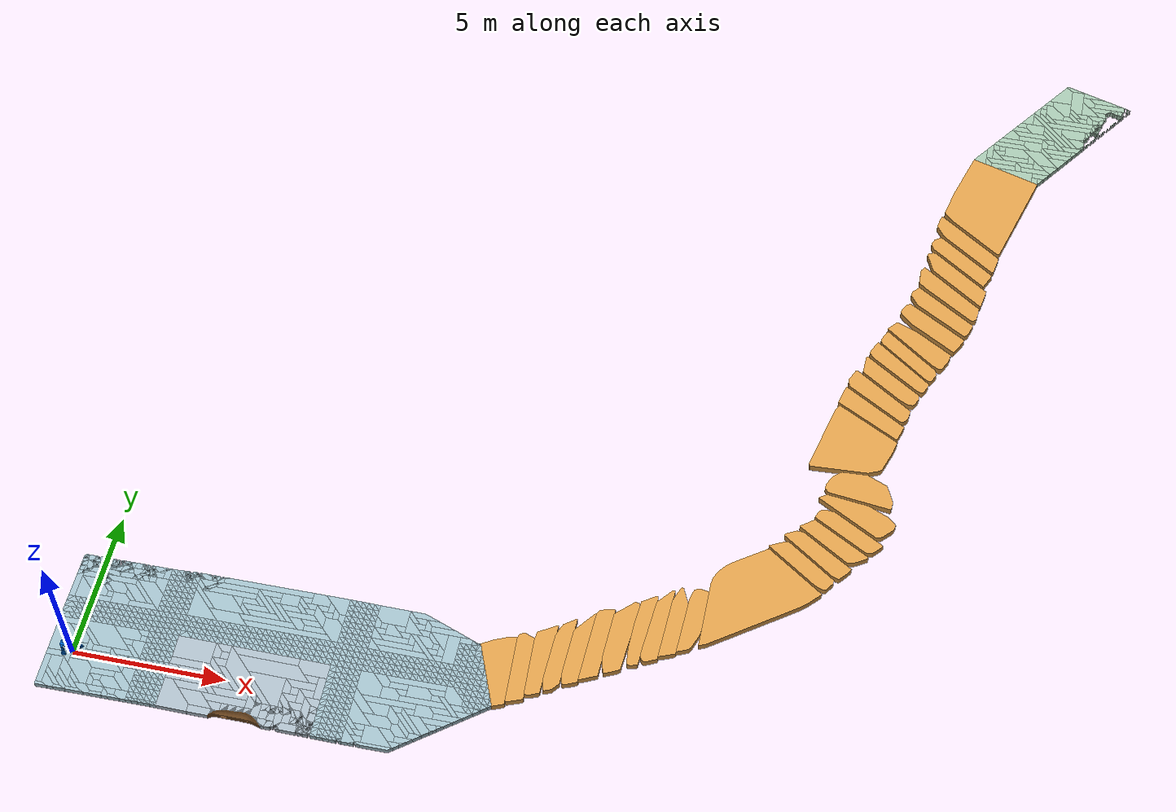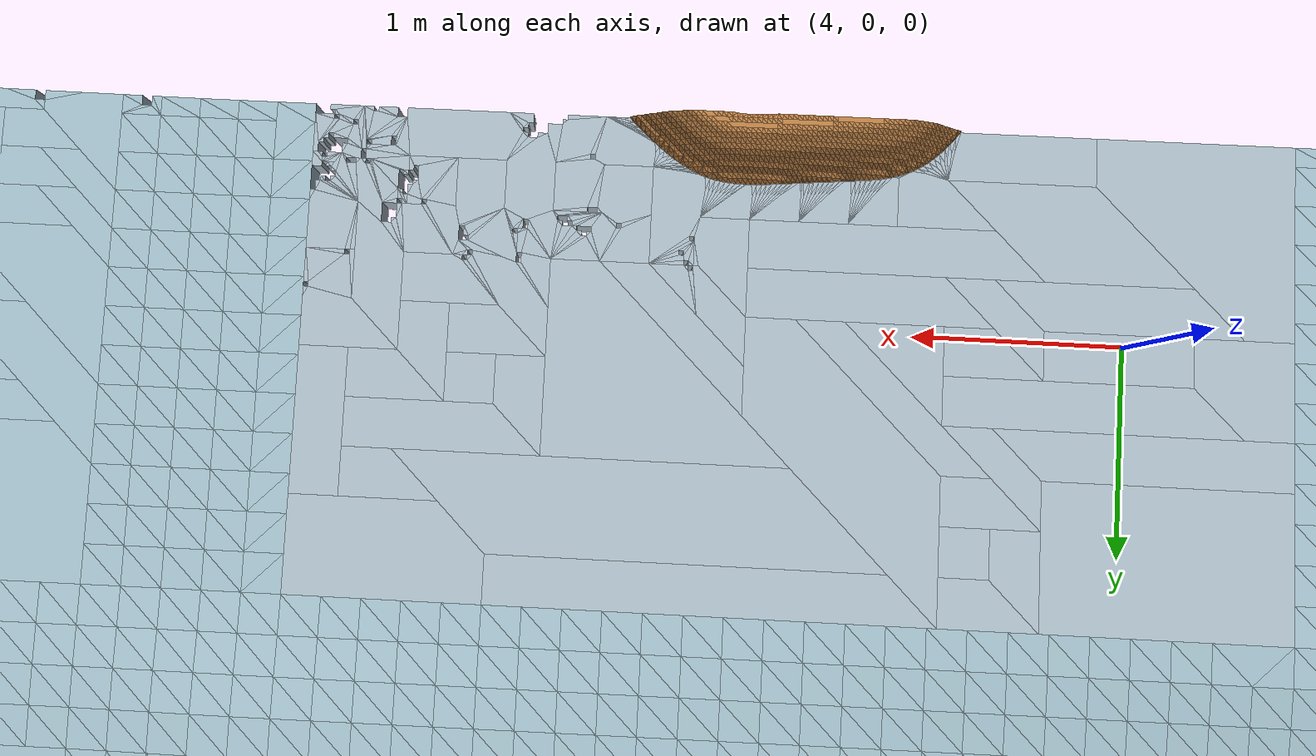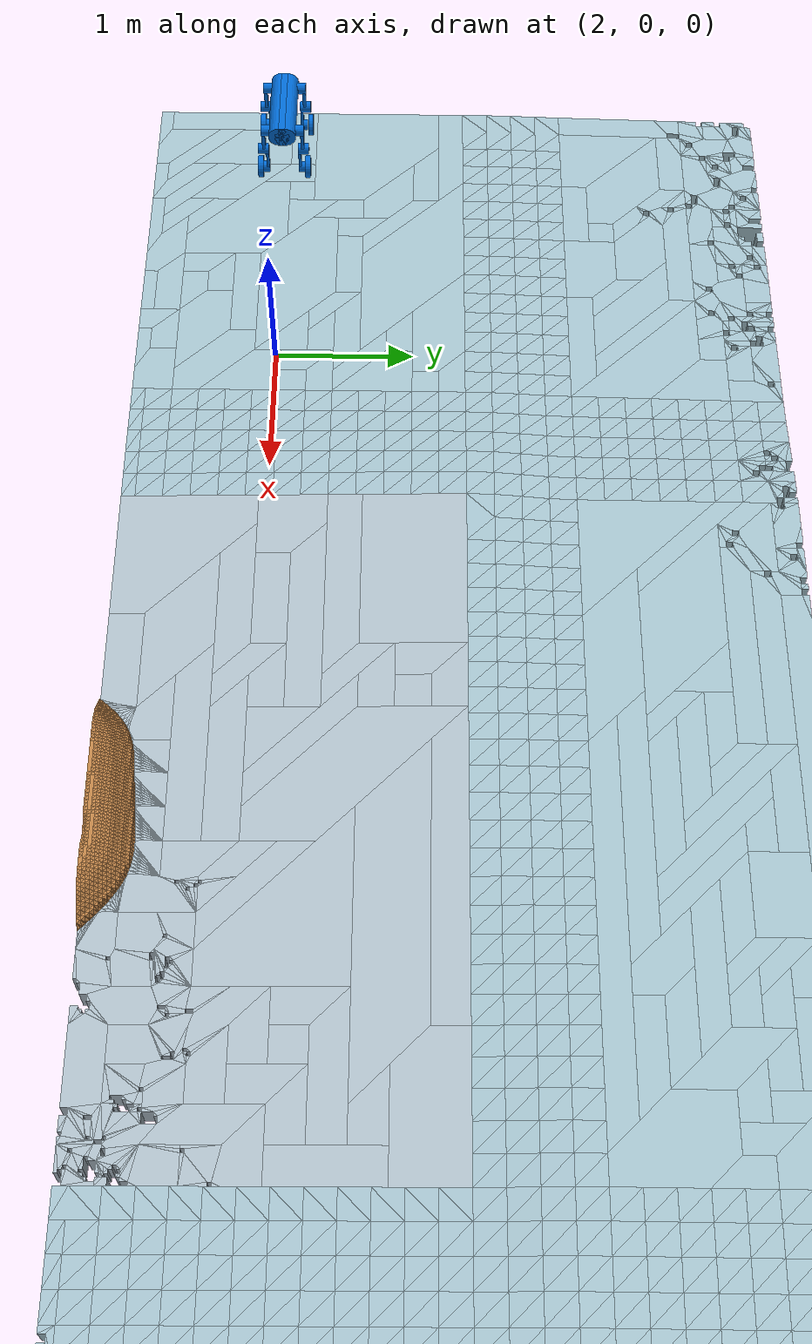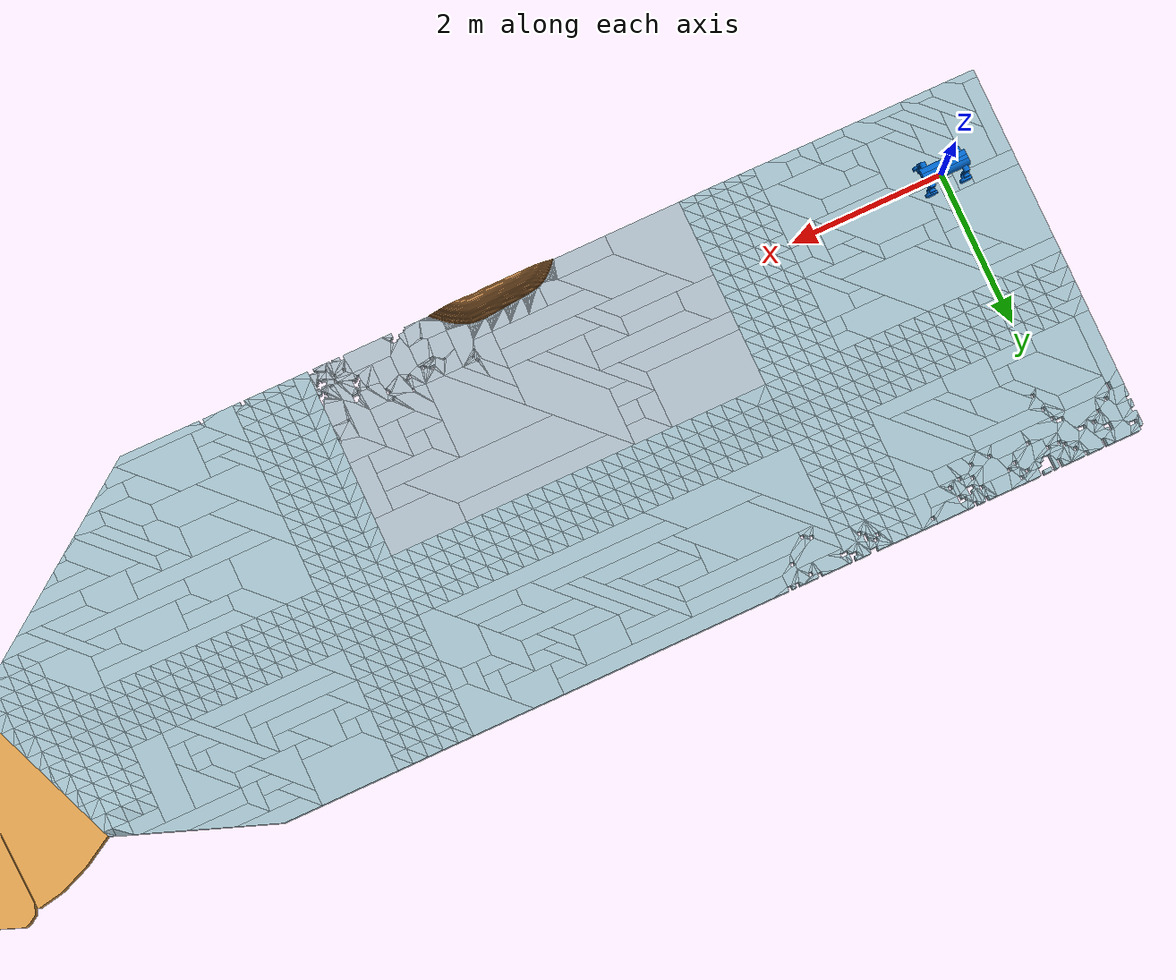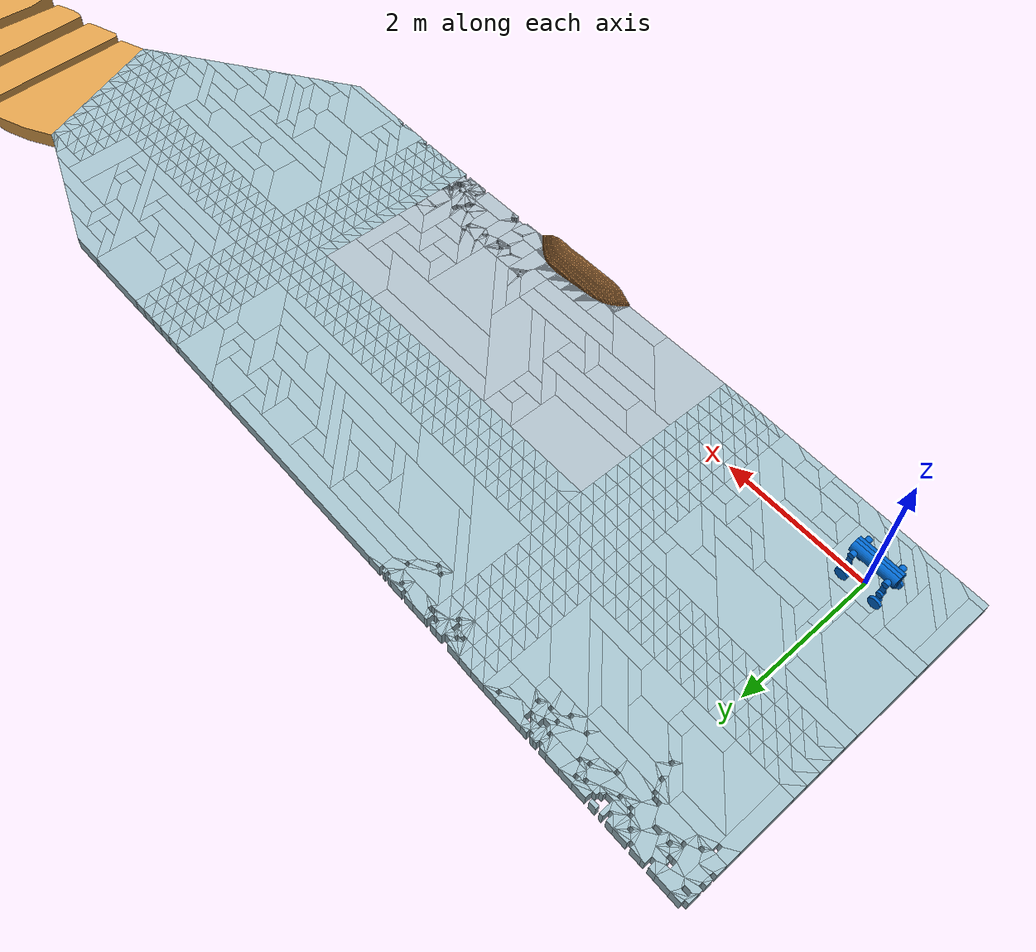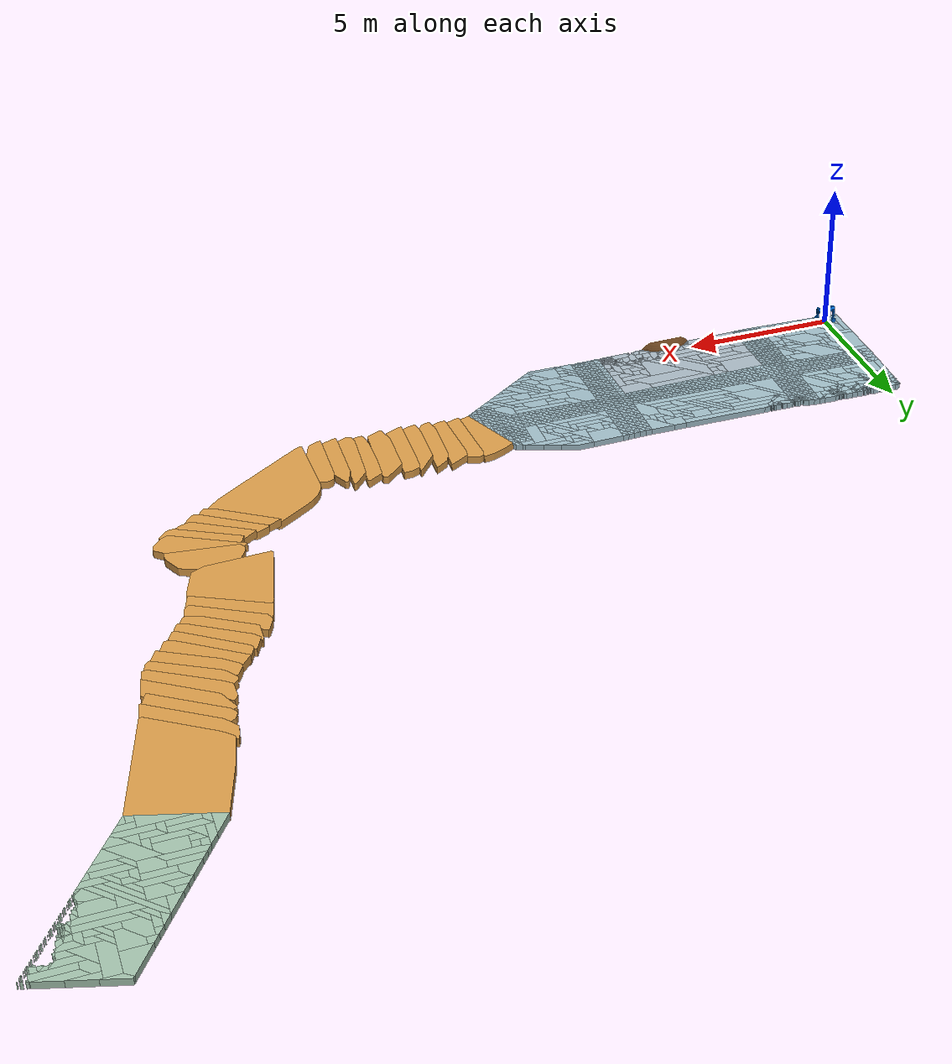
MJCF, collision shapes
<?xml version='1.0' encoding='utf-8'?>
<mujoco model="S10 official ONNX + full follower | Start B short | simulation only">
  <compiler angle="radian" />
  <option timestep=".001" integrator="implicitfast" gravity="0 0 -9.81" />
  <default>
    <geom solref=".01 1" />
    <default class="robot">
      <default class="motor">
        <joint />
        <motor />
      </default>
      <default class="visual">
        <geom material="default_material" contype="0" conaffinity="0" group="2" />
      </default>
      <default class="collision">
        <geom material="collision_material" condim="3" contype="1" conaffinity="1" solref="0.005 1" friction="1 0.01 0.001" density="0" group="1" />
      </default>
    </default>
  </default>
  <include file="../terrain/collision/new_surfaces.xml" />
  <include file="../terrain/collision/B_preserved.xml" />
  <asset>
    <mesh name="Start_sample_plane" file="../terrain/visual/Start_sample_plane.obj" inertia="shell" />
    <mesh name="Start_raised_band" file="../terrain/visual/Start_raised_band.obj" inertia="shell" />
    <mesh name="Start_remaining" file="../terrain/visual/Start_remaining.obj" inertia="shell" />
    <mesh name="Post_B_platform" file="../terrain/visual/Post_B_platform.obj" inertia="shell" />
    <mesh name="B_visual" file="../terrain/visual/B_preserved.obj" inertia="shell" />
    <material name="default_material" rgba="0.7 0.7 0.7 1" />
    <material name="collision_material" rgba="0.0 0.4 0.8 0.2" />
    <mesh name="base_link" file="robot/base_link.STL" />
    <mesh name="fl_hipx" file="robot/fl_hipx.STL" />
    <mesh name="fl_hipy" file="robot/fl_hipy.STL" />
    <mesh name="fl_knee" file="robot/fl_knee.STL" />
    <mesh name="fl_wheel" file="robot/fl_wheel.STL" />
    <mesh name="fr_hipx" file="robot/fr_hipx.STL" />
    <mesh name="fr_hipy" file="robot/fr_hipy.STL" />
    <mesh name="fr_knee" file="robot/fr_knee.STL" />
    <mesh name="fr_wheel" file="robot/fr_wheel.STL" />
    <mesh name="hl_hipx" file="robot/hl_hipx.STL" />
    <mesh name="hl_hipy" file="robot/hl_hipy.STL" />
    <mesh name="hl_knee" file="robot/hl_knee.STL" />
    <mesh name="hl_wheel" file="robot/hl_wheel.STL" />
    <mesh name="hr_hipx" file="robot/hr_hipx.STL" />
    <mesh name="hr_hipy" file="robot/hr_hipy.STL" />
    <mesh name="hr_knee" file="robot/hr_knee.STL" />
    <mesh name="hr_wheel" file="robot/hr_wheel.STL" />
    <texture name="texplane" type="2d" builtin="checker" rgb1=".2 .3 .4" rgb2=".1 0.15 0.2" width="512" height="512" />
    <material name="MatPlane" reflectance="0.3" texture="texplane" texrepeat="1 1" texuniform="true" />
  </asset>
  <worldbody>
    <geom name="Start_sample_plane" type="mesh" mesh="Start_sample_plane" group="2" contype="0" conaffinity="0" rgba="0.66 0.72 0.76 1" />
    <geom name="Start_raised_band" type="mesh" mesh="Start_raised_band" group="2" contype="0" conaffinity="0" rgba="0.73 0.5 0.27 1" />
    <geom name="Start_remaining" type="mesh" mesh="Start_remaining" group="2" contype="0" conaffinity="0" rgba="0.62 0.73 0.77 1" />
    <geom name="Post_B_platform" type="mesh" mesh="Post_B_platform" group="2" contype="0" conaffinity="0" rgba="0.63 0.75 0.67 1" />
    <geom name="B_visual" type="mesh" mesh="B_visual" group="2" contype="0" conaffinity="0" rgba=".88 .64 .34 1" />
    <body name="base_link" pos="0 0.0 0.5" quat="1 0 0 0" childclass="robot">
      <freejoint name="floating_base" />
      <inertial pos="-0.000512 0.057317 0.001182" quat="1 0 0 0" mass="8.023087" diaginertia="0.115559 0.171329 0.262028" />
      <site name="imu_site" pos="0.0075 -0.0373 0.0556" size="0.005" rgba="1 0 0 1" />
      <site name="base_site" pos="0 0 0" quat="1 0 0 0" />
      <geom type="mesh" class="visual" mesh="base_link" />
      <geom size="0.08 0.3" pos="0 0.024 0" quat="0.707107 0 0.707107 0" type="cylinder" class="collision" />
      <geom size="0.08 0.3" pos="0 -0.024 0" quat="0.707107 0 0.707107 0" type="cylinder" class="collision" />
      <geom size="0.08 0.024 0.3" quat="0.707107 0 0.707107 0" type="box" class="collision" />
      <body name="fl_hipx" pos="0.2277 0.0574 0">
        <inertial pos="-0.005034 0.023524 4.6e-05" quat="0.25609 0.665262 -0.228203 0.663151" mass="0.627405" diaginertia="0.000415056 0.000391723 0.000223221" />
        <joint name="fl_hipx_joint" pos="0 0 0" axis="-1 0 0" range="-0.6109 0.6109" actuatorfrcrange="-50 50" />
        <geom type="mesh" class="visual" mesh="fl_hipx" />
        <geom size="0.04 0.05" pos="0 0.054 0" quat="0.707107 0.707107 0 0" type="cylinder" class="collision" />
        <body name="fl_hipy" pos="0 0.0779 0">
          <inertial pos="7.4e-05 0.018439 -0.129675" quat="0.701304 -0.0510428 0.0516391 0.709155" mass="0.885874" diaginertia="0.00454086 0.00445199 0.00030515" />
          <joint name="fl_hipy_joint" pos="0 0 0" axis="0 -1 0" range="-2.5307 2.5307" actuatorfrcrange="-50 50" />
          <geom type="mesh" class="visual" mesh="fl_hipy" />
          <geom size="0.032 0.012 0.09" pos="0 0.012 -0.09" type="box" class="collision" />
          <geom size="0.04 0.04" pos="0 0.018 -0.18" quat="0.707107 0.707107 0 0" type="cylinder" class="collision" />
          <body name="fl_knee" pos="0 0 -0.18">
            <inertial pos="-3.2e-05 0.013504 -0.156308" quat="0.703786 -0.068447 0.068447 0.703786" mass="0.640283" diaginertia="0.0022296 0.002221 0.000193398" />
            <joint name="fl_knee_joint" pos="0 0 0" axis="0 -1 0" range="-2.7227 2.7227" actuatorfrcrange="-50 50" />
            <geom type="mesh" class="visual" mesh="fl_knee" />
            <geom size="0.029 0.01 0.09" pos="0 -0.012 -0.09" type="box" class="collision" />
            <geom size="0.04 0.025" pos="0 0.002 -0.18" quat="0.707107 0.707107 0 0" type="cylinder" class="collision" />
            <body name="fl_wheel" pos="0 0.045891 -0.18">
              <inertial pos="-8e-06 0.001694 -5e-06" quat="0.707107 0 0 0.707107" mass="0.587952" diaginertia="0.002003 0.001059 0.001059" />
              <joint name="fl_wheel_joint" pos="0 0 0" axis="0 -1 0" actuatorfrcrange="-14 14" />
              <geom type="mesh" class="visual" mesh="fl_wheel" />
              <geom size="0.081 0.0185" quat="0.707107 0.707107 0 0" type="cylinder" class="collision" />
            </body>
          </body>
        </body>
      </body>
      <body name="fr_hipx" pos="0.2277 -0.0574 0">
        <inertial pos="-0.004831 -0.02349 0.000169" quat="-0.278522 0.675499 0.205833 0.650968" mass="0.626546" diaginertia="0.000415238 0.000395047 0.000218715" />
        <joint name="fr_hipx_joint" pos="0 0 0" axis="-1 0 0" range="-0.6109 0.6109" actuatorfrcrange="-50 50" />
        <geom type="mesh" class="visual" mesh="fr_hipx" />
        <geom size="0.04 0.05" pos="0 -0.054 0" quat="0.707107 0.707107 0 0" type="cylinder" class="collision" />
        <body name="fr_hipy" pos="0 -0.0779 0">
          <inertial pos="-7.4e-05 -0.018439 -0.129675" quat="0.701304 0.0510428 -0.0516391 0.709155" mass="0.885874" diaginertia="0.00454086 0.00445199 0.00030515" />
          <joint name="fr_hipy_joint" pos="0 0 0" axis="0 -1 0" range="-2.5307 2.5307" actuatorfrcrange="-50 50" />
          <geom type="mesh" class="visual" mesh="fr_hipy" />
          <geom size="0.032 0.012 0.09" pos="0 -0.012 -0.09" type="box" class="collision" />
          <geom size="0.04 0.04" pos="0 -0.018 -0.18" quat="0.707107 0.707107 0 0" type="cylinder" class="collision" />
          <body name="fr_knee" pos="0 0 -0.18">
            <inertial pos="3.2e-05 -0.013504 -0.156308" quat="0.703786 0.068447 -0.068447 0.703786" mass="0.640283" diaginertia="0.0022296 0.002221 0.000193398" />
            <joint name="fr_knee_joint" pos="0 0 0" axis="0 -1 0" range="-2.7227 2.7227" actuatorfrcrange="-50 50" />
            <geom type="mesh" class="visual" mesh="fr_knee" />
            <geom size="0.029 0.01 0.09" pos="0 0.012 -0.09" type="box" class="collision" />
            <geom size="0.04 0.025" pos="0 -0.002 -0.18" quat="0.707107 0.707107 0 0" type="cylinder" class="collision" />
            <body name="fr_wheel" pos="0 -0.045891 -0.18">
              <inertial pos="8e-06 -0.001694 5e-06" quat="0.707107 0 0 0.707107" mass="0.587952" diaginertia="0.002003 0.001059 0.001059" />
              <joint name="fr_wheel_joint" pos="0 0 0" axis="0 -1 0" actuatorfrcrange="-14 14" />
              <geom type="mesh" class="visual" mesh="fr_wheel" />
              <geom size="0.081 0.0185" quat="0.707107 0.707107 0 0" type="cylinder" class="collision" />
            </body>
          </body>
        </body>
      </body>
      <body name="hl_hipx" pos="-0.2277 0.0574 0">
        <inertial pos="0.004831 0.02349 0.000169" quat="-0.205833 0.650968 0.278522 0.675499" mass="0.626546" diaginertia="0.000415238 0.000395047 0.000218715" />
        <joint name="hl_hipx_joint" pos="0 0 0" axis="-1 0 0" range="-0.6109 0.6109" actuatorfrcrange="-50 50" />
        <geom type="mesh" class="visual" mesh="hl_hipx" />
        <geom size="0.04 0.05" pos="0 0.054 0" quat="0.707107 0.707107 0 0" type="cylinder" class="collision" />
        <body name="hl_hipy" pos="0 0.0779 0">
          <inertial pos="7.4e-05 0.018439 -0.129675" quat="0.701304 -0.0510428 0.0516391 0.709155" mass="0.885874" diaginertia="0.00454086 0.00445199 0.00030515" />
          <joint name="hl_hipy_joint" pos="0 0 0" axis="0 -1 0" range="-2.5307 2.5307" actuatorfrcrange="-50 50" />
          <geom type="mesh" class="visual" mesh="hl_hipy" />
          <geom size="0.032 0.012 0.09" pos="0 0.012 -0.09" type="box" class="collision" />
          <geom size="0.04 0.04" pos="0 0.018 -0.18" quat="0.707107 0.707107 0 0" type="cylinder" class="collision" />
          <body name="hl_knee" pos="0 0 -0.18">
            <inertial pos="-3.2e-05 0.013504 -0.156308" quat="0.703786 -0.068447 0.068447 0.703786" mass="0.640283" diaginertia="0.0022296 0.002221 0.000193398" />
            <joint name="hl_knee_joint" pos="0 0 0" axis="0 -1 0" range="-2.7227 2.7227" actuatorfrcrange="-50 50" />
            <geom type="mesh" class="visual" mesh="hl_knee" />
            <geom size="0.029 0.01 0.09" pos="0 -0.012 -0.09" type="box" class="collision" />
            <geom size="0.04 0.025" pos="0 0.002 -0.18" quat="0.707107 0.707107 0 0" type="cylinder" class="collision" />
            <body name="hl_wheel" pos="0 0.054891 -0.18">
              <inertial pos="-8e-06 0.001694 -5e-06" quat="0.707107 0 0 0.707107" mass="0.587952" diaginertia="0.002003 0.001059 0.001059" />
              <joint name="hl_wheel_joint" pos="0 0 0" axis="0 -1 0" actuatorfrcrange="-14 14" />
              <geom type="mesh" class="visual" mesh="hl_wheel" />
              <geom size="0.081 0.0185" quat="0.707107 0.707107 0 0" type="cylinder" class="collision" />
            </body>
          </body>
        </body>
      </body>
      <body name="hr_hipx" pos="-0.2277 -0.0574 0">
        <inertial pos="0.005034 -0.023524 4.6e-05" quat="0.228203 0.663151 -0.25609 0.665262" mass="0.627405" diaginertia="0.000415056 0.000391723 0.000223221" />
        <joint name="hr_hipx_joint" pos="0 0 0" axis="-1 0 0" range="-0.6109 0.6109" actuatorfrcrange="-50 50" />
        <geom type="mesh" class="visual" mesh="hr_hipx" />
        <geom size="0.04 0.05" pos="0 -0.054 0" quat="0.707107 0.707107 0 0" type="cylinder" class="collision" />
        <body name="hr_hipy" pos="0 -0.0779 0">
          <inertial pos="-7.4e-05 -0.018439 -0.129675" quat="0.701304 0.0510428 -0.0516391 0.709155" mass="0.885874" diaginertia="0.00454086 0.00445199 0.00030515" />
          <joint name="hr_hipy_joint" pos="0 0 0" axis="0 -1 0" range="-2.5307 2.5307" actuatorfrcrange="-50 50" />
          <geom type="mesh" class="visual" mesh="hr_hipy" />
          <geom size="0.032 0.012 0.09" pos="0 -0.012 -0.09" type="box" class="collision" />
          <geom size="0.04 0.04" pos="0 -0.018 -0.18" quat="0.707107 0.707107 0 0" type="cylinder" class="collision" />
          <body name="hr_knee" pos="0 0 -0.18">
            <inertial pos="3.2e-05 -0.013504 -0.156308" quat="0.703786 0.068447 -0.068447 0.703786" mass="0.640283" diaginertia="0.0022296 0.002221 0.000193398" />
            <joint name="hr_knee_joint" pos="0 0 0" axis="0 -1 0" range="-2.7227 2.7227" actuatorfrcrange="-50 50" />
            <geom type="mesh" class="visual" mesh="hr_knee" />
            <geom size="0.029 0.01 0.09" pos="0 0.012 -0.09" type="box" class="collision" />
            <geom size="0.04 0.025" pos="0 -0.002 -0.18" quat="0.707107 0.707107 0 0" type="cylinder" class="collision" />
            <body name="hr_wheel" pos="0 -0.045891 -0.18">
              <inertial pos="8e-06 -0.001694 5e-06" quat="0.707107 0 0 0.707107" mass="0.587952" diaginertia="0.002003 0.001059 0.001059" />
              <joint name="hr_wheel_joint" pos="0 0 0" axis="0 -1 0" actuatorfrcrange="-14 14" />
              <geom type="mesh" class="visual" mesh="hr_wheel" />
              <geom size="0.081 0.0185" quat="0.707107 0.707107 0 0" type="cylinder" class="collision" />
            </body>
          </body>
        </body>
      </body>
    </body>
  </worldbody>
  <visual>
    <global offwidth="1600" offheight="1000" />
    <headlight ambient=".6 .6 .6" diffuse=".6 .6 .6" />
  </visual>
  <statistic center="14 11 2" extent="36" />
  <actuator>
    <motor name="fl_hipx_joint" joint="fl_hipx_joint" ctrllimited="true" ctrlrange="-50.00 50.00" gear="1" />
    <motor name="fl_hipy_joint" joint="fl_hipy_joint" ctrllimited="true" ctrlrange="-50.00 50.00" gear="1" />
    <motor name="fl_knee_joint" joint="fl_knee_joint" ctrllimited="true" ctrlrange="-50.00 50.00" gear="1" />
    <motor name="fl_wheel_joint" joint="fl_wheel_joint" ctrllimited="true" ctrlrange="-14.00 14.00" gear="1" />
    <motor name="fr_hipx_joint" joint="fr_hipx_joint" ctrllimited="true" ctrlrange="-50.00 50.00" gear="1" />
    <motor name="fr_hipy_joint" joint="fr_hipy_joint" ctrllimited="true" ctrlrange="-50.00 50.00" gear="1" />
    <motor name="fr_knee_joint" joint="fr_knee_joint" ctrllimited="true" ctrlrange="-50.00 50.00" gear="1" />
    <motor name="fr_wheel_joint" joint="fr_wheel_joint" ctrllimited="true" ctrlrange="-14.00 14.00" gear="1" />
    <motor name="hl_hipx_joint" joint="hl_hipx_joint" ctrllimited="true" ctrlrange="-50.00 50.00" gear="1" />
    <motor name="hl_hipy_joint" joint="hl_hipy_joint" ctrllimited="true" ctrlrange="-50.00 50.00" gear="1" />
    <motor name="hl_knee_joint" joint="hl_knee_joint" ctrllimited="true" ctrlrange="-50.00 50.00" gear="1" />
    <motor name="hl_wheel_joint" joint="hl_wheel_joint" ctrllimited="true" ctrlrange="-14.00 14.00" gear="1" />
    <motor name="hr_hipx_joint" joint="hr_hipx_joint" ctrllimited="true" ctrlrange="-50.00 50.00" gear="1" />
    <motor name="hr_hipy_joint" joint="hr_hipy_joint" ctrllimited="true" ctrlrange="-50.00 50.00" gear="1" />
    <motor name="hr_knee_joint" joint="hr_knee_joint" ctrllimited="true" ctrlrange="-50.00 50.00" gear="1" />
    <motor name="hr_wheel_joint" joint="hr_wheel_joint" ctrllimited="true" ctrlrange="-14.00 14.00" gear="1" />
  </actuator>
  <contact>
    <exclude body1="base_link" body2="fl_hipx" />
    <exclude body1="fl_hipx" body2="fl_hipy" />
    <exclude body1="fl_hipy" body2="fl_knee" />
    <exclude body1="fl_knee" body2="fl_wheel" />
    <exclude body1="base_link" body2="fr_hipx" />
    <exclude body1="fr_hipx" body2="fr_hipy" />
    <exclude body1="fr_hipy" body2="fr_knee" />
    <exclude body1="fr_knee" body2="fr_wheel" />
    <exclude body1="base_link" body2="hl_hipx" />
    <exclude body1="hl_hipx" body2="hl_hipy" />
    <exclude body1="hl_hipy" body2="hl_knee" />
    <exclude body1="hl_knee" body2="hl_wheel" />
    <exclude body1="base_link" body2="hr_hipx" />
    <exclude body1="hr_hipx" body2="hr_hipy" />
    <exclude body1="hr_hipy" body2="hr_knee" />
    <exclude body1="hr_knee" body2="hr_wheel" />
  </contact>
  <sensor>
    <framequat name="base_quat" objtype="site" objname="base_site" />
    <accelerometer site="imu_site" />
    <gyro site="imu_site" />
  </sensor>
<keyframe><key name="start_pose" qpos="0 0.5 0.002767465092347543 1 0 0 0 0 -0.29999999999999999 0.59999999999999998 0 0 -0.29999999999999999 0.59999999999999998 0 0 0.29999999999999999 -0.59999999999999998 0 0 0.29999999999999999 -0.59999999999999998 0" /></keyframe></mujoco>

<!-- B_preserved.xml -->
<mujocoinclude>
  <asset>
    <mesh name="B_surface_000" vertex="-0.789859444 0.305321584 0.124531843 0.047366021 -1.767114825 0.085751592 0.407266974 -1.623256114 0.092320345 0.427412470 -1.614911577 0.092694591 0.315681563 0.747555184 0.144717091 0.303806329 0.752474067 0.144717430 0.014433036 0.698196609 0.140814679 -0.033849332 0.686230986 0.140098158 -0.121569785 0.650424233 0.138480427 -0.163996192 0.632850640 0.137692267 -0.406691640 0.532229213 0.133181579 -0.789859444 0.305321584 -0.125468157 0.047366021 -1.767114825 -0.164248408 0.407266974 -1.623256114 -0.157679655 0.427412470 -1.614911577 -0.157305409 0.315681563 0.747555184 -0.105282909 0.303806329 0.752474067 -0.105282570 0.014433036 0.698196609 -0.109185321 -0.033849332 0.686230986 -0.109901842 -0.121569785 0.650424233 -0.111519573 -0.163996192 0.632850640 -0.112307733 -0.406691640 0.532229213 -0.116818421" />
    <mesh name="B_surface_001" vertex="0.383679659 -1.214619878 0.101279165 0.281698561 0.941694428 0.148762103 0.275403128 0.944302082 0.148762282 -0.062295585 1.075240409 0.148571115 -0.090836936 1.076288098 0.148329944 -0.133263343 1.058714505 0.147541784 -0.233388391 0.992662507 0.145129731 -0.250961985 0.950236100 0.144013892 -0.281215907 0.856408195 0.141626024 -0.175900732 -1.370402695 0.092590723 -0.154525190 -1.386438543 0.092428816 -0.112098783 -1.404012136 0.092427605 0.255639548 -1.268823332 0.098874327 0.298065955 -1.251249739 0.099662488 0.383679659 -1.214619878 -0.148720835 0.281698561 0.941694428 -0.101237897 0.275403128 0.944302082 -0.101237718 -0.062295585 1.075240409 -0.101428885 -0.090836936 1.076288098 -0.101670056 -0.133263343 1.058714505 -0.102458216 -0.233388391 0.992662507 -0.104870269 -0.250961985 0.950236100 -0.105986108 -0.281215907 0.856408195 -0.108373976 -0.175900732 -1.370402695 -0.157409277 -0.154525190 -1.386438543 -0.157571184 -0.112098783 -1.404012136 -0.157572395 0.255639548 -1.268823332 -0.151125673 0.298065955 -1.251249739 -0.150337512" />
    <mesh name="B_surface_002" vertex="0.278266993 -0.963558611 0.105940132 0.372720109 1.462059452 0.161293159 0.339418537 1.475853415 0.161294110 0.296992130 1.458279822 0.160505949 -0.236838795 1.132064520 0.148228566 -0.254412389 1.089638113 0.147112727 -0.292330745 0.860164105 0.141607296 -0.200233672 -1.087159864 0.098726413 -0.176437131 -1.097016714 0.098725734 -0.135786341 -1.102054318 0.098989601 -0.074063022 -1.096988979 0.099675804 0.020138960 -1.074427267 0.101056174 0.062565367 -1.056853674 0.101844335 0.278266993 -0.963558611 -0.144059868 0.372720109 1.462059452 -0.088706841 0.339418537 1.475853415 -0.088705890 0.296992130 1.458279822 -0.089494051 -0.236838795 1.132064520 -0.101771434 -0.254412389 1.089638113 -0.102887273 -0.292330745 0.860164105 -0.108392704 -0.200233672 -1.087159864 -0.151273587 -0.176437131 -1.097016714 -0.151274266 -0.135786341 -1.102054318 -0.151010399 -0.074063022 -1.096988979 -0.150324196 0.020138960 -1.074427267 -0.148943826 0.062565367 -1.056853674 -0.148155665" />
    <mesh name="B_surface_003" vertex="-0.224857695 0.763002522 0.140050905 -0.285957038 -0.806068739 0.104244425 -0.222050309 -1.133818690 0.097476167 -0.204476716 -1.176245097 0.096686293 -0.162050309 -1.193818690 0.096685082 0.024407496 -1.117451852 0.100129471 0.066833903 -1.099878259 0.100917632 0.083437791 -1.081504748 0.101484273 0.259484448 -0.860668041 0.108076760 0.350587817 1.478926339 0.161466712 0.342532826 1.482262826 0.161466942 0.300106419 1.464689233 0.160678781 -0.057555481 1.209361521 0.151627307 -0.126434778 1.056819041 0.147562544 -0.144008371 1.014392634 0.146446705 -0.224857695 0.763002522 -0.109949095 -0.285957038 -0.806068739 -0.145755575 -0.222050309 -1.133818690 -0.152523833 -0.204476716 -1.176245097 -0.153313707 -0.162050309 -1.193818690 -0.153314918 0.024407496 -1.117451852 -0.149870529 0.066833903 -1.099878259 -0.149082368 0.083437791 -1.081504748 -0.148515727 0.259484448 -0.860668041 -0.141923240 0.350587817 1.478926339 -0.088533288 0.342532826 1.482262826 -0.088533058 0.300106419 1.464689233 -0.089321219 -0.057555481 1.209361521 -0.098372693 -0.126434778 1.056819041 -0.102437456 -0.144008371 1.014392634 -0.103553295" />
    <mesh name="B_surface_004" vertex="0.277055284 -0.875690749 0.107902321 0.373106832 1.590976118 0.164192090 0.354536868 1.598668049 0.164192620 0.312110462 1.581094456 0.163404459 -0.177500629 0.940876446 0.144484985 -0.225795480 0.858578554 0.142188753 -0.283686158 -0.628092074 0.108262670 -0.230377450 -0.986124104 0.100716017 -0.212803857 -1.028550511 0.099926143 -0.170377450 -1.046124104 0.099924932 -0.029347415 -1.011592838 0.102008424 0.013078992 -0.994019245 0.102796585 0.277055284 -0.875690749 -0.142097679 0.373106832 1.590976118 -0.085807910 0.354536868 1.598668049 -0.085807380 0.312110462 1.581094456 -0.086595541 -0.177500629 0.940876446 -0.105515015 -0.225795480 0.858578554 -0.107811247 -0.283686158 -0.628092074 -0.141737330 -0.230377450 -0.986124104 -0.149283983 -0.212803857 -1.028550511 -0.150073857 -0.170377450 -1.046124104 -0.150075068 -0.029347415 -1.011592838 -0.147991576 0.013078992 -0.994019245 -0.147203415" />
    <mesh name="B_surface_005" vertex="-0.252128844 -1.619770874 0.086283193 -0.232405976 -1.627940353 0.086282630 -0.164818950 -1.608596380 0.087343898 -0.122392543 -1.591022786 0.088132059 0.327453502 -1.383522744 0.096964312 0.420257512 0.999745218 0.151350903 0.401909744 1.007345112 0.151351427 0.124528564 0.971824846 0.147981163 0.082102157 0.954251253 0.147193002 -0.050077271 0.892017377 0.144569419 -0.095968061 0.868700563 0.143620141 -0.126907671 0.807411050 0.141956695 -0.144481265 0.764984643 0.140840856 -0.167070898 0.564573075 0.136130303 -0.252128844 -1.619770874 -0.163716807 -0.232405976 -1.627940353 -0.163717370 -0.164818950 -1.608596380 -0.162656102 -0.122392543 -1.591022786 -0.161867941 0.327453502 -1.383522744 -0.153035688 0.420257512 0.999745218 -0.098649097 0.401909744 1.007345112 -0.098648573 0.124528564 0.971824846 -0.102018837 0.082102157 0.954251253 -0.102806998 -0.050077271 0.892017377 -0.105430581 -0.095968061 0.868700563 -0.106379859 -0.126907671 0.807411050 -0.108043305 -0.144481265 0.764984643 -0.109159144 -0.167070898 0.564573075 -0.113869697" />
    <mesh name="B_surface_006" vertex="-0.453785688 -0.706685193 0.104919992 -0.338738126 -1.196792826 0.094979632 -0.321164533 -1.239219233 0.094189758 -0.278738126 -1.256792826 0.094188547 -0.236311720 -1.239219233 0.094976708 0.136205118 -1.066637673 0.102307552 0.176172396 -1.024426098 0.103626252 0.189527582 -1.006736793 0.104147396 0.192124073 -1.000468309 0.104312261 0.363876517 1.149578862 0.154193129 0.346527914 1.333686073 0.158167103 0.328954321 1.376112480 0.158956977 0.286527914 1.393686073 0.158958188 0.212692376 1.401071152 0.158439277 0.170265970 1.383497559 0.157651117 -0.380320248 0.865963492 0.140921505 -0.393815739 0.833382494 0.140064606 -0.453785688 -0.706685193 -0.145080008 -0.338738126 -1.196792826 -0.155020368 -0.321164533 -1.239219233 -0.155810242 -0.278738126 -1.256792826 -0.155811453 -0.236311720 -1.239219233 -0.155023292 0.136205118 -1.066637673 -0.147692448 0.176172396 -1.024426098 -0.146373748 0.189527582 -1.006736793 -0.145852604 0.192124073 -1.000468309 -0.145687739 0.363876517 1.149578862 -0.095806871 0.346527914 1.333686073 -0.091832897 0.328954321 1.376112480 -0.091043023 0.286527914 1.393686073 -0.091041812 0.212692376 1.401071152 -0.091560723 0.170265970 1.383497559 -0.092348883 -0.380320248 0.865963492 -0.109078495 -0.393815739 0.833382494 -0.109935394" />
    <mesh name="B_surface_007" vertex="-0.262607009 -0.411451530 0.113323702 -0.217521854 -0.894168088 0.102900486 -0.199948261 -0.936594495 0.102110613 -0.187422929 -0.964686046 0.101595867 -0.144996522 -0.982259639 0.101594656 -0.084500616 -0.988155631 0.102023294 0.092012156 -0.937793682 0.104791406 0.134438563 -0.920220088 0.105579567 0.138188332 -0.918392038 0.105655399 0.333170294 1.522449027 0.162282655 0.317343648 1.560657932 0.162994009 0.274917241 1.578231525 0.162995220 0.232490834 1.560657932 0.162207059 -0.178819024 1.291020057 0.152336646 -0.246744850 0.440704765 0.132609421 -0.262607009 -0.411451530 -0.136676298 -0.217521854 -0.894168088 -0.147099514 -0.199948261 -0.936594495 -0.147889387 -0.187422929 -0.964686046 -0.148404133 -0.144996522 -0.982259639 -0.148405344 -0.084500616 -0.988155631 -0.147976706 0.092012156 -0.937793682 -0.145208594 0.134438563 -0.920220088 -0.144420433 0.138188332 -0.918392038 -0.144344601 0.333170294 1.522449027 -0.087717345 0.317343648 1.560657932 -0.087005991 0.274917241 1.578231525 -0.087004780 0.232490834 1.560657932 -0.087792941 -0.178819024 1.291020057 -0.097663354 -0.246744850 0.440704765 -0.117390579" />
    <mesh name="B_surface_008" vertex="-0.166340121 1.021151887 0.146391400 -0.314453311 -0.832972218 0.103375916 -0.275001356 -1.012913548 0.099700496 -0.257427763 -1.055339955 0.098910623 -0.184631342 -1.103100328 0.098513106 -0.142204935 -1.120673921 0.098511895 -0.099778528 -1.103100328 0.099300056 0.243594393 -0.942335099 0.106095228 0.340017052 1.533862139 0.162602481 0.307208942 1.547451703 0.162603417 0.295721688 1.542771632 0.162391771 0.253295281 1.525198038 0.161603611 -0.166340121 1.021151887 -0.103608600 -0.314453311 -0.832972218 -0.146624084 -0.275001356 -1.012913548 -0.150299504 -0.257427763 -1.055339955 -0.151089377 -0.184631342 -1.103100328 -0.151486894 -0.142204935 -1.120673921 -0.151488105 -0.099778528 -1.103100328 -0.150699944 0.243594393 -0.942335099 -0.143904772 0.340017052 1.533862139 -0.087397519 0.307208942 1.547451703 -0.087396583 0.295721688 1.542771632 -0.087608229 0.253295281 1.525198038 -0.088396389" />
    <mesh name="B_surface_009" vertex="0.251251047 -1.118436135 0.102211178 0.320827308 0.668327948 0.142985447 0.072843447 1.203066946 0.152695294 0.030417041 1.220640539 0.152696506 -0.012009366 1.203066946 0.151908345 -0.029582959 1.160640539 0.150792506 -0.203026118 0.691410524 0.138645490 -0.281231082 -1.316944323 0.092814482 -0.272115834 -1.320719982 0.092814222 -0.095673406 -1.258968064 0.095837489 0.218299923 -1.132084938 0.101599041 0.251251047 -1.118436135 -0.147788822 0.320827308 0.668327948 -0.107014553 0.072843447 1.203066946 -0.097304706 0.030417041 1.220640539 -0.097303494 -0.012009366 1.203066946 -0.098091655 -0.029582959 1.160640539 -0.099207494 -0.203026118 0.691410524 -0.111354510 -0.281231082 -1.316944323 -0.157185518 -0.272115834 -1.320719982 -0.157185778 -0.095673406 -1.258968064 -0.154162511 0.218299923 -1.132084938 -0.148400959" />
    <mesh name="B_surface_010" vertex="0.323293698 -0.240850337 0.122589053 0.317569517 1.078127255 0.152158930 0.307450334 1.082318758 0.152159219 0.001635078 1.128243632 0.150354428 -0.040791328 1.110670039 0.149566267 -0.088825486 1.088128531 0.148614524 -0.153253123 1.044730290 0.147042321 -0.170826716 1.002303884 0.145926482 -0.248395247 0.741456219 0.139348702 -0.324068299 -1.201877482 0.095001488 -0.319167664 -1.203907391 0.095001348 -0.131542451 -1.127644640 0.098454226 -0.089116044 -1.110071047 0.099242387 0.058644033 -1.040041332 0.102185557 0.118058936 -0.961346334 0.104504001 0.135632529 -0.918919927 0.105619840 0.303702235 -0.471320119 0.117231227 0.323293698 -0.240850337 -0.127410947 0.317569517 1.078127255 -0.097841070 0.307450334 1.082318758 -0.097840781 0.001635078 1.128243632 -0.099645572 -0.040791328 1.110670039 -0.100433733 -0.088825486 1.088128531 -0.101385476 -0.153253123 1.044730290 -0.102957679 -0.170826716 1.002303884 -0.104073518 -0.248395247 0.741456219 -0.110651298 -0.324068299 -1.201877482 -0.154998512 -0.319167664 -1.203907391 -0.154998652 -0.131542451 -1.127644640 -0.151545774 -0.089116044 -1.110071047 -0.150757613 0.058644033 -1.040041332 -0.147814443 0.118058936 -0.961346334 -0.145495999 0.135632529 -0.918919927 -0.144380160 0.303702235 -0.471320119 -0.132768773" />
    <mesh name="B_surface_011" vertex="-1.407781528 -0.094441216 0.109822767 -1.397977939 -2.353404682 0.059179548 -1.175497636 -2.255691494 0.063437439 -0.779399012 -1.984816042 0.073194574 0.987377781 -0.752130517 0.117265102 1.560892629 -0.345168088 0.131724028 1.674584139 -0.242602131 0.135081969 1.738691338 -0.181967259 0.137038318 2.070919381 0.166130655 0.147937441 2.079492545 0.186828106 0.148481796 0.207644855 1.481289963 0.160194102 0.172170768 1.474923166 0.159722113 0.129744361 1.457349572 0.158933953 -0.110417281 1.294652245 0.153052599 -0.780962145 0.834279372 0.136494241 -1.009408612 0.659927098 0.130459778 -1.232705974 0.391402847 0.122358058 -1.354897039 0.152932407 0.115869006 -1.372470632 0.110506000 0.114753168 -1.407781528 -0.094441216 -0.140177233 -1.397977939 -2.353404682 -0.190820452 -1.175497636 -2.255691494 -0.186562561 -0.779399012 -1.984816042 -0.176805426 0.987377781 -0.752130517 -0.132734898 1.560892629 -0.345168088 -0.118275972 1.674584139 -0.242602131 -0.114918031 1.738691338 -0.181967259 -0.112961682 2.070919381 0.166130655 -0.102062559 2.079492545 0.186828106 -0.101518204 0.207644855 1.481289963 -0.089805898 0.172170768 1.474923166 -0.090277887 0.129744361 1.457349572 -0.091066047 -0.110417281 1.294652245 -0.096947401 -0.780962145 0.834279372 -0.113505759 -1.009408612 0.659927098 -0.119540222 -1.232705974 0.391402847 -0.127641942 -1.354897039 0.152932407 -0.134130994 -1.372470632 0.110506000 -0.135246832" />
    <mesh name="B_surface_012" vertex="1.043968155 -0.314301714 0.127623150 -0.578367121 0.807611754 0.137774237 -0.617194611 0.796345226 0.137161104 -0.659621018 0.778771633 0.136372943 -0.883479959 0.684325267 0.132175636 -1.129931890 0.561133779 0.127123208 -1.156957053 0.545295857 0.126516864 -1.159946641 0.541932879 0.126413608 -1.167512963 0.523666163 0.125933183 0.483614259 -0.618158153 0.115601943 0.511544769 -0.629511526 0.115605993 0.727653683 -0.710980388 0.115780537 0.800767360 -0.721089437 0.116231575 0.843193767 -0.703515844 0.117019736 0.872162834 -0.673335636 0.117966222 1.026266419 -0.455308134 0.124292111 1.043840012 -0.412881727 0.125407950 1.043968155 -0.314301714 -0.122376850 -0.578367121 0.807611754 -0.112225763 -0.617194611 0.796345226 -0.112838896 -0.659621018 0.778771633 -0.113627057 -0.883479959 0.684325267 -0.117824364 -1.129931890 0.561133779 -0.122876792 -1.156957053 0.545295857 -0.123483136 -1.159946641 0.541932879 -0.123586392 -1.167512963 0.523666163 -0.124066817 0.483614259 -0.618158153 -0.134398057 0.511544769 -0.629511526 -0.134394007 0.727653683 -0.710980388 -0.134219463 0.800767360 -0.721089437 -0.133768425 0.843193767 -0.703515844 -0.132980264 0.872162834 -0.673335636 -0.132033778 1.026266419 -0.455308134 -0.125707889 1.043840012 -0.412881727 -0.124592050" />
    <mesh name="B_surface_013" vertex="-1.253051319 0.536118086 0.125419534 0.452613112 -0.643421018 0.114747050 0.476322903 -0.652071395 0.114772662 0.658321433 -0.704867070 0.115274829 0.700747840 -0.687293477 0.116062990 0.904099397 -0.462125228 0.123005993 1.003476028 -0.321670169 0.127082126 1.021049621 -0.279243762 0.128197965 1.020638606 -0.278251485 0.128216438 -0.668502831 0.772587434 0.136151680 -0.894482024 0.782046257 0.134268319 -0.936908431 0.764472664 0.133480158 -1.233375371 0.608072785 0.127218048 -1.250948964 0.565646378 0.126102209 -1.253051319 0.536118086 -0.124580466 0.452613112 -0.643421018 -0.135252950 0.476322903 -0.652071395 -0.135227338 0.658321433 -0.704867070 -0.134725171 0.700747840 -0.687293477 -0.133937010 0.904099397 -0.462125228 -0.126994007 1.003476028 -0.321670169 -0.122917874 1.021049621 -0.279243762 -0.121802035 1.020638606 -0.278251485 -0.121783562 -0.668502831 0.772587434 -0.113848320 -0.894482024 0.782046257 -0.115731681 -0.936908431 0.764472664 -0.116519842 -1.233375371 0.608072785 -0.122781952 -1.250948964 0.565646378 -0.123897791" />
    <mesh name="B_surface_014" vertex="-1.332706146 0.440659897 0.122536893 0.342252355 -0.601355616 0.114668280 0.597505454 -0.521299387 0.118833557 0.639931861 -0.503725794 0.119621718 0.949153984 -0.311654810 0.126803263 0.966727577 -0.269228403 0.127919102 0.961937477 -0.257664078 0.128134400 -0.899979506 0.781221792 0.134198817 -0.901070866 0.780769736 0.134178543 -1.323752189 0.462276662 0.123105426 -1.332706146 0.440659897 -0.127463107 0.342252355 -0.601355616 -0.135331720 0.597505454 -0.521299387 -0.131166443 0.639931861 -0.503725794 -0.130378282 0.949153984 -0.311654810 -0.123196737 0.966727577 -0.269228403 -0.122080898 0.961937477 -0.257664078 -0.121865600 -0.899979506 0.781221792 -0.115801183 -0.901070866 0.780769736 -0.115821457 -1.323752189 0.462276662 -0.126894574" />
    <mesh name="B_surface_015" vertex="-0.929713388 0.184915477 0.120530592 0.860326014 -0.813865166 0.114700286 1.022359870 -0.783042964 0.116895272 1.064786276 -0.765469371 0.117683433 1.335276143 -0.477718037 0.126654652 1.347939512 -0.447145961 0.127458715 -0.349304687 0.499858139 0.132986779 -0.390269669 0.502228081 0.132660084 -0.678171886 0.518687747 0.130359664 -0.720598293 0.501114154 0.129571503 -0.815414834 0.441524977 0.127353832 -0.830350628 0.422977318 0.126798750 -0.916864430 0.215935606 0.121346439 -0.929713388 0.184915477 -0.129469408 0.860326014 -0.813865166 -0.135299714 1.022359870 -0.783042964 -0.133104728 1.064786276 -0.765469371 -0.132316567 1.335276143 -0.477718037 -0.123345348 1.347939512 -0.447145961 -0.122541285 -0.349304687 0.499858139 -0.117013221 -0.390269669 0.502228081 -0.117339916 -0.678171886 0.518687747 -0.119640336 -0.720598293 0.501114154 -0.120428497 -0.815414834 0.441524977 -0.122646168 -0.830350628 0.422977318 -0.123201250 -0.916864430 0.215935606 -0.128653561" />
    <mesh name="B_surface_016" vertex="-1.686923275 0.481135335 0.120160820 0.312653280 -0.634559859 0.113648035 0.418290662 -0.596985156 0.115471638 0.460717069 -0.579411562 0.116259799 0.509408076 -0.546938134 0.117440695 0.803964505 -0.243797358 0.126980746 0.821538098 -0.201370951 0.128096585 0.852848920 -0.079864433 0.131115890 0.835275327 -0.037438026 0.131905764 0.823671548 -0.017791123 0.132239397 0.593714300 0.185116490 0.134663816 -0.090316748 0.488220137 0.135127330 -1.444668969 0.660564889 0.126437371 -1.537792902 0.606873586 0.124367858 -1.672379893 0.516246165 0.121084255 -1.686923275 0.481135335 -0.129839180 0.312653280 -0.634559859 -0.136351965 0.418290662 -0.596985156 -0.134528362 0.460717069 -0.579411562 -0.133740201 0.509408076 -0.546938134 -0.132559305 0.803964505 -0.243797358 -0.123019254 0.821538098 -0.201370951 -0.121903415 0.852848920 -0.079864433 -0.118884110 0.835275327 -0.037438026 -0.118094236 0.823671548 -0.017791123 -0.117760603 0.593714300 0.185116490 -0.115336184 -0.090316748 0.488220137 -0.114872670 -1.444668969 0.660564889 -0.123562629 -1.537792902 0.606873586 -0.125632142 -1.672379893 0.516246165 -0.128915745" />
    <mesh name="B_surface_017" vertex="0.216974073 0.600031880 0.140488418 -0.589720481 0.560788614 0.132125533 -0.732337252 0.462833463 0.128602885 -0.750227255 0.449140717 0.128129442 -0.831587352 0.369899404 0.125595202 -0.926889256 0.210828886 0.121138774 -1.004657198 0.074447824 0.117354544 -1.022230791 0.032021417 0.116238705 -1.044064310 -0.113364784 0.112770981 -1.026490716 -0.155791191 0.111981108 -0.932856842 -0.277518225 0.110115624 1.106486233 -0.537029800 0.123200703 1.115948029 -0.533110596 0.123376476 1.118338781 -0.531735190 0.123429539 1.135912374 -0.489308783 0.124545377 1.149890418 -0.264923423 0.129714493 1.132316825 -0.222497017 0.130504366 1.009462392 0.054010717 0.135575075 0.875732328 0.311276089 0.140112756 0.216974073 0.600031880 -0.109511582 -0.589720481 0.560788614 -0.117874467 -0.732337252 0.462833463 -0.121397115 -0.750227255 0.449140717 -0.121870558 -0.831587352 0.369899404 -0.124404798 -0.926889256 0.210828886 -0.128861226 -1.004657198 0.074447824 -0.132645456 -1.022230791 0.032021417 -0.133761295 -1.044064310 -0.113364784 -0.137229019 -1.026490716 -0.155791191 -0.138018892 -0.932856842 -0.277518225 -0.139884376 1.106486233 -0.537029800 -0.126799297 1.115948029 -0.533110596 -0.126623524 1.118338781 -0.531735190 -0.126570461 1.135912374 -0.489308783 -0.125454623 1.149890418 -0.264923423 -0.120285507 1.132316825 -0.222497017 -0.119495634 1.009462392 0.054010717 -0.114424925 0.875732328 0.311276089 -0.109887244" />
    <mesh name="B_surface_018" vertex="-0.994667195 1.319621133 0.145412586 -1.491992582 -0.830784133 0.092504218 -1.474418989 -0.873210540 0.091714344 -1.451027860 -0.913929280 0.091016777 0.412141298 -0.823291700 0.110331980 0.706038229 -0.698613724 0.115857813 0.821884042 -0.630617293 0.118459335 0.839457635 -0.588190887 0.119575173 1.034240823 -0.024512807 0.134041315 1.085822878 0.129646287 0.137981967 1.172354372 0.490756543 0.146894673 1.166036134 0.506010118 0.147178656 -0.848775184 1.575068745 0.152502738 -0.977093602 1.362047539 0.146528425 -0.994667195 1.319621133 -0.104587414 -1.491992582 -0.830784133 -0.157495782 -1.474418989 -0.873210540 -0.158285656 -1.451027860 -0.913929280 -0.158983223 0.412141298 -0.823291700 -0.139668020 0.706038229 -0.698613724 -0.134142187 0.821884042 -0.630617293 -0.131540665 0.839457635 -0.588190887 -0.130424827 1.034240823 -0.024512807 -0.115958685 1.085822878 0.129646287 -0.112018033 1.172354372 0.490756543 -0.103105327 1.166036134 0.506010118 -0.102821344 -0.848775184 1.575068745 -0.097497262 -0.977093602 1.362047539 -0.103471575" />
    <mesh name="B_surface_019" vertex="-1.113798749 0.252789454 0.120347715 0.928182205 -0.830685378 0.114951838 0.954361840 -0.819841418 0.115438181 0.971935433 -0.777415011 0.116554020 1.119291732 -0.314148425 0.128325165 1.116288346 -0.306897608 0.128460157 -0.928316283 0.902924512 0.136669339 -0.945624587 0.861138569 0.135570345 -1.012958804 0.670829686 0.130671714 -1.089361131 0.361305620 0.123011525 -1.113798749 0.252789454 -0.129652285 0.928182205 -0.830685378 -0.135048162 0.954361840 -0.819841418 -0.134561819 0.971935433 -0.777415011 -0.133445980 1.119291732 -0.314148425 -0.121674835 1.116288346 -0.306897608 -0.121539843 -0.928316283 0.902924512 -0.113330661 -0.945624587 0.861138569 -0.114429655 -1.012958804 0.670829686 -0.119328286 -1.089361131 0.361305620 -0.126988475" />
    <mesh name="B_surface_020" vertex="1.244320902 -0.399270772 0.127572956 -0.665962951 0.855808299 0.138044295 -0.666697985 0.855553296 0.138031751 -0.709124392 0.837979703 0.137243591 -0.726817167 0.806658888 0.136376067 -0.875365192 0.478145984 0.127620307 -0.892938785 0.435719577 0.126504468 -0.866605245 0.302486918 0.123756416 -0.849031652 0.260060511 0.122966543 -0.822625821 0.205415645 0.121984167 -0.800316159 0.173286933 0.121469493 0.965244980 -0.871421120 0.114380684 1.021405681 -0.890084763 0.114482367 1.063832088 -0.872511170 0.115270528 1.170207016 -0.778169525 0.118375902 1.196450544 -0.721042404 0.119902312 1.214024138 -0.678615997 0.121018151 1.244320902 -0.399270772 -0.122427044 -0.665962951 0.855808299 -0.111955705 -0.666697985 0.855553296 -0.111968249 -0.709124392 0.837979703 -0.112756409 -0.726817167 0.806658888 -0.113623933 -0.875365192 0.478145984 -0.122379693 -0.892938785 0.435719577 -0.123495532 -0.866605245 0.302486918 -0.126243584 -0.849031652 0.260060511 -0.127033457 -0.822625821 0.205415645 -0.128015833 -0.800316159 0.173286933 -0.128530507 0.965244980 -0.871421120 -0.135619316 1.021405681 -0.890084763 -0.135517633 1.063832088 -0.872511170 -0.134729472 1.170207016 -0.778169525 -0.131624098 1.196450544 -0.721042404 -0.130097688 1.214024138 -0.678615997 -0.128981849" />
    <mesh name="B_surface_021" vertex="-1.010176211 0.985246225 0.137759013 -1.033892949 0.446428416 0.125437729 -1.021201451 0.413404263 0.124813743 -1.006293216 0.377412601 0.124143668 0.299700314 -0.480640585 0.116984784 0.474601270 -0.555538431 0.116924732 0.517027677 -0.573112024 0.116923521 0.605284035 -0.606079666 0.117001615 0.725598396 -0.598417761 0.118289524 0.768024803 -0.580844168 0.119077685 0.874192134 -0.380062380 0.124571677 0.891765727 -0.337635973 0.125687516 0.876928205 -0.175300484 0.129195807 -0.968956116 1.037467334 0.139314136 -0.992602618 1.027672632 0.138874852 -1.010176211 0.985246225 -0.112240987 -1.033892949 0.446428416 -0.124562271 -1.021201451 0.413404263 -0.125186257 -1.006293216 0.377412601 -0.125856332 0.299700314 -0.480640585 -0.133015216 0.474601270 -0.555538431 -0.133075268 0.517027677 -0.573112024 -0.133076479 0.605284035 -0.606079666 -0.132998385 0.725598396 -0.598417761 -0.131710476 0.768024803 -0.580844168 -0.130922315 0.874192134 -0.380062380 -0.125428323 0.891765727 -0.337635973 -0.124312484 0.876928205 -0.175300484 -0.120804193 -0.968956116 1.037467334 -0.110685864 -0.992602618 1.027672632 -0.111125148" />
    <mesh name="B_surface_022" vertex="-0.919667429 1.057199133 0.140214410 -0.963384315 0.973241352 0.137923357 -1.112096775 0.652308777 0.129336318 -1.129670368 0.609882370 0.128220479 -1.112096775 0.567455963 0.127430606 -0.991257249 0.410528754 0.125026873 0.570037163 -0.615260129 0.116468541 0.624065030 -0.633937362 0.116550138 0.735991632 -0.664694789 0.116897396 0.778418039 -0.647121196 0.117685557 0.802462032 -0.613750458 0.118658022 0.894757089 -0.429964842 0.123641641 0.912330682 -0.387538436 0.124757480 0.910111246 -0.278349138 0.127189182 -0.919667429 1.057199133 -0.109785590 -0.963384315 0.973241352 -0.112076643 -1.112096775 0.652308777 -0.120663682 -1.129670368 0.609882370 -0.121779521 -1.112096775 0.567455963 -0.122569394 -0.991257249 0.410528754 -0.124973127 0.570037163 -0.615260129 -0.133531459 0.624065030 -0.633937362 -0.133449862 0.735991632 -0.664694789 -0.133102604 0.778418039 -0.647121196 -0.132314443 0.802462032 -0.613750458 -0.131341978 0.894757089 -0.429964842 -0.126358359 0.912330682 -0.387538436 -0.125242520 0.910111246 -0.278349138 -0.122810818" />
    <mesh name="B_surface_023" vertex="1.066619985 -0.551041239 0.122516288 1.009840667 -0.366095861 0.126143395 -0.706122386 0.886378834 0.138358430 -0.757290147 0.812110229 0.136215884 -0.828422938 0.654759452 0.132022231 -0.845996531 0.612333045 0.130906393 -0.870702498 0.544747446 0.129159355 -0.887164553 0.482444082 0.127607407 -0.869590960 0.440017675 0.126817534 -0.833970994 0.367522603 0.125519714 0.774055007 -0.806169261 0.114073027 0.878425547 -0.833626779 0.114424320 0.889423502 -0.833743087 0.114523706 0.931849909 -0.816169494 0.115311867 1.049046392 -0.593467646 0.121400449 1.066619985 -0.551041239 -0.127483712 1.009840667 -0.366095861 -0.123856605 -0.706122386 0.886378834 -0.111641570 -0.757290147 0.812110229 -0.113784116 -0.828422938 0.654759452 -0.117977769 -0.845996531 0.612333045 -0.119093607 -0.870702498 0.544747446 -0.120840645 -0.887164553 0.482444082 -0.122392593 -0.869590960 0.440017675 -0.123182466 -0.833970994 0.367522603 -0.124480286 0.774055007 -0.806169261 -0.135926973 0.878425547 -0.833626779 -0.135575680 0.889423502 -0.833743087 -0.135476294 0.931849909 -0.816169494 -0.134688133 1.049046392 -0.593467646 -0.128599551" />
    <mesh name="B_surface_024" vertex="-1.365952635 0.618341128 0.126219105 0.224047417 -0.542193667 0.114900734 0.430411603 -0.646625689 0.114469173 0.472838010 -0.664199282 0.114467962 0.535570037 -0.645813696 0.115462679 0.577996444 -0.628240102 0.116250840 0.730536668 -0.320753369 0.124571398 0.748110262 -0.278326963 0.125687236 0.790886298 -0.031534072 0.131626684 0.789668858 -0.028594913 0.131681404 -0.379849899 0.659128016 0.136280541 -1.077504678 0.943007283 0.136185943 -1.119931084 0.925433690 0.135397783 -1.356827300 0.640371635 0.126798520 -1.365952635 0.618341128 -0.123780895 0.224047417 -0.542193667 -0.135099266 0.430411603 -0.646625689 -0.135530827 0.472838010 -0.664199282 -0.135532038 0.535570037 -0.645813696 -0.134537321 0.577996444 -0.628240102 -0.133749160 0.730536668 -0.320753369 -0.125428602 0.748110262 -0.278326963 -0.124312764 0.790886298 -0.031534072 -0.118373316 0.789668858 -0.028594913 -0.118318596 -0.379849899 0.659128016 -0.113719459 -1.077504678 0.943007283 -0.113814057 -1.119931084 0.925433690 -0.114602217 -1.356827300 0.640371635 -0.123201480" />
    <mesh name="B_surface_025" vertex="-0.546086825 -0.043198204 0.118965242 0.900912498 -0.894090595 0.113274911 0.915344213 -0.888112783 0.113543011 0.987219649 -0.768562477 0.116894589 1.026604464 -0.694767329 0.118917223 1.171673923 -0.415063643 0.126544515 1.189247516 -0.372637236 0.127660353 1.171673923 -0.330210829 0.128450227 1.168659939 -0.327389992 0.128485628 -0.719328443 0.782821274 0.135910150 -0.729928535 0.778430572 0.135713231 -0.821341225 0.725459560 0.133675765 -0.898187403 0.602379376 0.130198809 -0.972371497 0.462237306 0.126363349 -0.989945090 0.419810900 0.125247510 -0.980996704 0.370026477 0.124212390 -0.963423111 0.327600070 0.123422516 -0.909727292 0.265267555 0.122520579 -0.546086825 -0.043198204 -0.131034758 0.900912498 -0.894090595 -0.136725089 0.915344213 -0.888112783 -0.136456989 0.987219649 -0.768562477 -0.133105411 1.026604464 -0.694767329 -0.131082777 1.171673923 -0.415063643 -0.123455485 1.189247516 -0.372637236 -0.122339647 1.171673923 -0.330210829 -0.121549773 1.168659939 -0.327389992 -0.121514372 -0.719328443 0.782821274 -0.114089850 -0.729928535 0.778430572 -0.114286769 -0.821341225 0.725459560 -0.116324235 -0.898187403 0.602379376 -0.119801191 -0.972371497 0.462237306 -0.123636651 -0.989945090 0.419810900 -0.124752490 -0.980996704 0.370026477 -0.125787610 -0.963423111 0.327600070 -0.126577484 -0.909727292 0.265267555 -0.127479421" />
    <mesh name="B_surface_026" vertex="1.156922319 -0.350844882 0.127849995 -0.738385654 0.850283976 0.137248555 -0.779076058 0.833429459 0.136492645 -0.957296208 0.654941756 0.130831118 -0.974869801 0.612515349 0.129715279 -0.989038914 0.516735154 0.127432740 -0.971465321 0.474308747 0.126642866 -0.733194386 0.140593666 0.121357741 0.910971509 -0.826240408 0.114892051 0.943127850 -0.812920815 0.115489424 1.024608651 -0.736541555 0.117960505 1.045061209 -0.699343427 0.118985622 1.062634802 -0.656917020 0.120101461 1.156922319 -0.350844882 -0.122150005 -0.738385654 0.850283976 -0.112751445 -0.779076058 0.833429459 -0.113507355 -0.957296208 0.654941756 -0.119168882 -0.974869801 0.612515349 -0.120284721 -0.989038914 0.516735154 -0.122567260 -0.971465321 0.474308747 -0.123357134 -0.733194386 0.140593666 -0.128642259 0.910971509 -0.826240408 -0.135107949 0.943127850 -0.812920815 -0.134510576 1.024608651 -0.736541555 -0.132039495 1.045061209 -0.699343427 -0.131014378 1.062634802 -0.656917020 -0.129898539" />
    <mesh name="B_surface_027" vertex="1.042400342 -0.307726117 0.127756291 -0.903246539 1.044046662 0.140071311 -0.915285494 1.039059964 0.139847662 -1.005392398 0.917701609 0.136286392 -1.022965991 0.875275203 0.135170554 -1.019860754 0.420217363 0.124979192 -1.002287161 0.377790957 0.124189319 -0.798801747 0.206358009 0.122226283 0.841001627 -0.832847853 0.114094733 0.844711401 -0.832216640 0.114143315 0.936637545 -0.803658766 0.115637247 0.979063952 -0.786085173 0.116425408 0.996637545 -0.743658766 0.117541247 1.027387669 -0.574256452 0.121631045 1.042400342 -0.307726117 -0.122243709 -0.903246539 1.044046662 -0.109928689 -0.915285494 1.039059964 -0.110152338 -1.005392398 0.917701609 -0.113713608 -1.022965991 0.875275203 -0.114829446 -1.019860754 0.420217363 -0.125020808 -1.002287161 0.377790957 -0.125810681 -0.798801747 0.206358009 -0.127773717 0.841001627 -0.832847853 -0.135905267 0.844711401 -0.832216640 -0.135856685 0.936637545 -0.803658766 -0.134362753 0.979063952 -0.786085173 -0.133574592 0.996637545 -0.743658766 -0.132458753 1.027387669 -0.574256452 -0.128368955" />
    <mesh name="B_surface_028" vertex="-0.732355994 0.103013478 0.120521502 0.955037440 -1.069333125 0.109841104 0.958934646 -1.067718849 0.109913502 0.976508239 -1.025292442 0.111029341 1.040698098 -0.692208912 0.119105391 1.080263077 -0.445463210 0.125013999 1.077791070 -0.432850113 0.125274351 -0.740207785 0.830236929 0.136781419 -0.804848670 0.838870692 0.136375827 -0.847275077 0.821297099 0.135587666 -0.982323817 0.755575891 0.132859150 -0.999897410 0.713149484 0.131743311 -0.982323817 0.670723077 0.130953438 -0.732355994 0.103013478 -0.129478498 0.955037440 -1.069333125 -0.140158896 0.958934646 -1.067718849 -0.140086498 0.976508239 -1.025292442 -0.138970659 1.040698098 -0.692208912 -0.130894609 1.080263077 -0.445463210 -0.124986001 1.077791070 -0.432850113 -0.124725649 -0.740207785 0.830236929 -0.113218581 -0.804848670 0.838870692 -0.113624173 -0.847275077 0.821297099 -0.114412334 -0.982323817 0.755575891 -0.117140850 -0.999897410 0.713149484 -0.118256689 -0.982323817 0.670723077 -0.119046562" />
    <mesh name="B_surface_029" vertex="1.432779947 -0.605056982 0.124699020 -0.384552275 0.657566905 0.136201869 -0.393403244 0.653900714 0.136037444 -0.601464389 0.529091646 0.131304733 -0.664434370 0.386501156 0.127518286 -0.682007963 0.344074749 0.126402447 -0.665124419 0.280575090 0.125132889 -0.647550826 0.238148683 0.124343016 -0.633124333 0.205656366 0.123747065 -0.577845430 0.125613121 0.122462044 1.184658082 -1.098917545 0.111306234 1.208909178 -1.088872412 0.111756750 1.423160040 -0.628281492 0.124088202 1.432779947 -0.605056982 -0.125300980 -0.384552275 0.657566905 -0.113798131 -0.393403244 0.653900714 -0.113962556 -0.601464389 0.529091646 -0.118695267 -0.664434370 0.386501156 -0.122481714 -0.682007963 0.344074749 -0.123597553 -0.665124419 0.280575090 -0.124867111 -0.647550826 0.238148683 -0.125656984 -0.633124333 0.205656366 -0.126252935 -0.577845430 0.125613121 -0.127537956 1.184658082 -1.098917545 -0.138693766 1.208909178 -1.088872412 -0.138243250 1.423160040 -0.628281492 -0.125911798" />
    <mesh name="B_surface_030" vertex="-0.646854175 0.073614072 0.120654188 1.075385610 -1.122942653 0.109753229 1.115481114 -1.106334552 0.110498088 1.133054708 -1.063908145 0.111613927 1.231054459 -0.533221105 0.124441524 1.217158685 -0.499673739 0.125066092 -0.807899254 0.907271285 0.137883746 -0.808407358 0.906555527 0.137862959 -0.825980951 0.864129120 0.136747120 -0.873949023 0.694883276 0.132501152 -0.913308705 0.461026661 0.126883924 -0.895735112 0.418600254 0.126094051 -0.646854175 0.073614072 -0.129345812 1.075385610 -1.122942653 -0.140246771 1.115481114 -1.106334552 -0.139501912 1.133054708 -1.063908145 -0.138386073 1.231054459 -0.533221105 -0.125558476 1.217158685 -0.499673739 -0.124933908 -0.807899254 0.907271285 -0.112116254 -0.808407358 0.906555527 -0.112137041 -0.825980951 0.864129120 -0.113252880 -0.873949023 0.694883276 -0.117498848 -0.913308705 0.461026661 -0.123116076 -0.895735112 0.418600254 -0.123905949" />
    <mesh name="B_surface_031" vertex="1.427525549 1.571064429 0.173523877 -0.776433863 2.247610623 0.168278294 -1.271004592 0.643111775 0.127656005 -1.460590200 -0.208393317 0.106773750 -1.443016607 -0.250819724 0.105983877 -1.185582340 -0.511491126 0.102516968 0.411514074 -1.621102268 0.092408108 0.463679343 -1.629562188 0.092701902 0.506105750 -1.611988595 0.093490062 0.523679343 -1.569562188 0.094605901 1.387289249 1.416392305 0.169676928 1.416834294 1.524740274 0.172384328 1.427525549 1.571064429 -0.076476123 -0.776433863 2.247610623 -0.081721706 -1.271004592 0.643111775 -0.122343995 -1.460590200 -0.208393317 -0.143226250 -1.443016607 -0.250819724 -0.144016123 -1.185582340 -0.511491126 -0.147483032 0.411514074 -1.621102268 -0.157591892 0.463679343 -1.629562188 -0.157298098 0.506105750 -1.611988595 -0.156509938 0.523679343 -1.569562188 -0.155394099 1.387289249 1.416392305 -0.080323072 1.416834294 1.524740274 -0.077615672" />
  </asset>
  <worldbody>
    <geom name="B_surface_000" type="mesh" mesh="B_surface_000" pos="13.275328332 2.757332535 -0.454369501" contype="1" conaffinity="1" group="3" friction=".8 .005 .0001" solref=".006 1" solimp=".95 .99 .001" rgba=".85 .61 .29 1" />
    <geom name="B_surface_001" type="mesh" mesh="B_surface_001" pos="13.875425337 2.580827739 -0.337209159" contype="1" conaffinity="1" group="3" friction=".8 .005 .0001" solref=".006 1" solimp=".95 .99 .001" rgba=".85 .61 .29 1" />
    <geom name="B_surface_002" type="mesh" mesh="B_surface_002" pos="14.454678654 2.551900253 -0.164975711" contype="1" conaffinity="1" group="3" friction=".8 .005 .0001" solref=".006 1" solimp=".95 .99 .001" rgba=".85 .61 .29 1" />
    <geom name="B_surface_003" type="mesh" mesh="B_surface_003" pos="15.034909171 2.805467450 0.005706447" contype="1" conaffinity="1" group="3" friction=".8 .005 .0001" solref=".006 1" solimp=".95 .99 .001" rgba=".85 .61 .29 1" />
    <geom name="B_surface_004" type="mesh" mesh="B_surface_004" pos="15.591190659 2.909587571 0.169398087" contype="1" conaffinity="1" group="3" friction=".8 .005 .0001" solref=".006 1" solimp=".95 .99 .001" rgba=".85 .61 .29 1" />
    <geom name="B_surface_005" type="mesh" mesh="B_surface_005" pos="16.121463586 3.681628749 0.335821161" contype="1" conaffinity="1" group="3" friction=".8 .005 .0001" solref=".006 1" solimp=".95 .99 .001" rgba=".85 .61 .29 1" />
    <geom name="B_surface_006" type="mesh" mesh="B_surface_006" pos="16.925276629 3.584502589 0.512661959" contype="1" conaffinity="1" group="3" friction=".8 .005 .0001" solref=".006 1" solimp=".95 .99 .001" rgba=".85 .61 .29 1" />
    <geom name="B_surface_007" type="mesh" mesh="B_surface_007" pos="17.485489715 3.662351128 0.671546964" contype="1" conaffinity="1" group="3" friction=".8 .005 .0001" solref=".006 1" solimp=".95 .99 .001" rgba=".85 .61 .29 1" />
    <geom name="B_surface_008" type="mesh" mesh="B_surface_008" pos="17.965950026 3.925173504 0.821906325" contype="1" conaffinity="1" group="3" friction=".8 .005 .0001" solref=".006 1" solimp=".95 .99 .001" rgba=".85 .61 .29 1" />
    <geom name="B_surface_009" type="mesh" mesh="B_surface_009" pos="18.491159779 4.309651260 0.993252917" contype="1" conaffinity="1" group="3" friction=".8 .005 .0001" solref=".006 1" solimp=".95 .99 .001" rgba=".85 .61 .29 1" />
    <geom name="B_surface_010" type="mesh" mesh="B_surface_010" pos="19.066370352 4.390299217 1.138825144" contype="1" conaffinity="1" group="3" friction=".8 .005 .0001" solref=".006 1" solimp=".95 .99 .001" rgba=".85 .61 .29 1" />
    <geom name="B_surface_011" type="mesh" mesh="B_surface_011" pos="20.790593382 5.822787119 1.295086253" contype="1" conaffinity="1" group="3" friction=".8 .005 .0001" solref=".006 1" solimp=".95 .99 .001" rgba=".85 .61 .29 1" />
    <geom name="B_surface_012" type="mesh" mesh="B_surface_012" pos="22.123386093 6.809708182 1.469369575" contype="1" conaffinity="1" group="3" friction=".8 .005 .0001" solref=".006 1" solimp=".95 .99 .001" rgba=".85 .61 .29 1" />
    <geom name="B_surface_013" type="mesh" mesh="B_surface_013" pos="22.638146442 7.191795956 1.614859597" contype="1" conaffinity="1" group="3" friction=".8 .005 .0001" solref=".006 1" solimp=".95 .99 .001" rgba=".85 .61 .29 1" />
    <geom name="B_surface_014" type="mesh" mesh="B_surface_014" pos="23.146791507 7.620498494 1.774468986" contype="1" conaffinity="1" group="3" friction=".8 .005 .0001" solref=".006 1" solimp=".95 .99 .001" rgba=".85 .61 .29 1" />
    <geom name="B_surface_015" type="mesh" mesh="B_surface_015" pos="23.164581921 8.223468855 1.923234281" contype="1" conaffinity="1" group="3" friction=".8 .005 .0001" solref=".006 1" solimp=".95 .99 .001" rgba=".85 .61 .29 1" />
    <geom name="B_surface_016" type="mesh" mesh="B_surface_016" pos="23.942157544 8.554676441 2.098658974" contype="1" conaffinity="1" group="3" friction=".8 .005 .0001" solref=".006 1" solimp=".95 .99 .001" rgba=".85 .61 .29 1" />
    <geom name="B_surface_017" type="mesh" mesh="B_surface_017" pos="23.438860070 9.491676045 2.253114705" contype="1" conaffinity="1" group="3" friction=".8 .005 .0001" solref=".006 1" solimp=".95 .99 .001" rgba=".85 .61 .29 1" />
    <geom name="B_surface_018" type="mesh" mesh="B_surface_018" pos="23.246450614 10.915133782 2.403512452" contype="1" conaffinity="1" group="3" friction=".8 .005 .0001" solref=".006 1" solimp=".95 .99 .001" rgba=".85 .61 .29 1" />
    <geom name="B_surface_019" type="mesh" mesh="B_surface_019" pos="23.436115120 12.277398580 2.547329892" contype="1" conaffinity="1" group="3" friction=".8 .005 .0001" solref=".006 1" solimp=".95 .99 .001" rgba=".85 .61 .29 1" />
    <geom name="B_surface_020" type="mesh" mesh="B_surface_020" pos="23.423630363 12.938684046 2.691968454" contype="1" conaffinity="1" group="3" friction=".8 .005 .0001" solref=".006 1" solimp=".95 .99 .001" rgba=".85 .61 .29 1" />
    <geom name="B_surface_021" type="mesh" mesh="B_surface_021" pos="23.976283206 13.277581301 2.837243392" contype="1" conaffinity="1" group="3" friction=".8 .005 .0001" solref=".006 1" solimp=".95 .99 .001" rgba=".85 .61 .29 1" />
    <geom name="B_surface_022" type="mesh" mesh="B_surface_022" pos="24.185771209 13.781535895 2.997440207" contype="1" conaffinity="1" group="3" friction=".8 .005 .0001" solref=".006 1" solimp=".95 .99 .001" rgba=".85 .61 .29 1" />
    <geom name="B_surface_023" type="mesh" mesh="B_surface_023" pos="24.235771483 14.372167929 3.107912703" contype="1" conaffinity="1" group="3" friction=".8 .005 .0001" solref=".006 1" solimp=".95 .99 .001" rgba=".85 .61 .29 1" />
    <geom name="B_surface_024" type="mesh" mesh="B_surface_024" pos="24.871811018 14.657570383 3.231283842" contype="1" conaffinity="1" group="3" friction=".8 .005 .0001" solref=".006 1" solimp=".95 .99 .001" rgba=".85 .61 .29 1" />
    <geom name="B_surface_025" type="mesh" mesh="B_surface_025" pos="24.821341682 15.487328390 3.461775630" contype="1" conaffinity="1" group="3" friction=".8 .005 .0001" solref=".006 1" solimp=".95 .99 .001" rgba=".85 .61 .29 1" />
    <geom name="B_surface_026" type="mesh" mesh="B_surface_026" pos="25.060365240 15.997154483 3.644940935" contype="1" conaffinity="1" group="3" friction=".8 .005 .0001" solref=".006 1" solimp=".95 .99 .001" rgba=".85 .61 .29 1" />
    <geom name="B_surface_027" type="mesh" mesh="B_surface_027" pos="25.279786692 16.540312697 3.824979661" contype="1" conaffinity="1" group="3" friction=".8 .005 .0001" solref=".006 1" solimp=".95 .99 .001" rgba=".85 .61 .29 1" />
    <geom name="B_surface_028" type="mesh" mesh="B_surface_028" pos="25.384286648 17.290013432 3.991534353" contype="1" conaffinity="1" group="3" friction=".8 .005 .0001" solref=".006 1" solimp=".95 .99 .001" rgba=".85 .61 .29 1" />
    <geom name="B_surface_029" type="mesh" mesh="B_surface_029" pos="25.141186331 18.050731376 4.131980647" contype="1" conaffinity="1" group="3" friction=".8 .005 .0001" solref=".006 1" solimp=".95 .99 .001" rgba=".85 .61 .29 1" />
    <geom name="B_surface_030" type="mesh" mesh="B_surface_030" pos="25.466569981 18.590857042 4.285289766" contype="1" conaffinity="1" group="3" friction=".8 .005 .0001" solref=".006 1" solimp=".95 .99 .001" rgba=".85 .61 .29 1" />
    <geom name="B_surface_031" type="mesh" mesh="B_surface_031" pos="26.188566892 19.770401298 4.462677467" contype="1" conaffinity="1" group="3" friction=".8 .005 .0001" solref=".006 1" solimp=".95 .99 .001" rgba=".85 .61 .29 1" />
  </worldbody>
</mujocoinclude>
